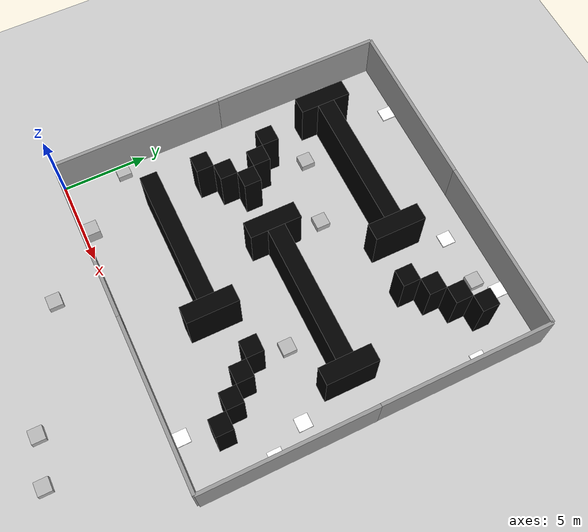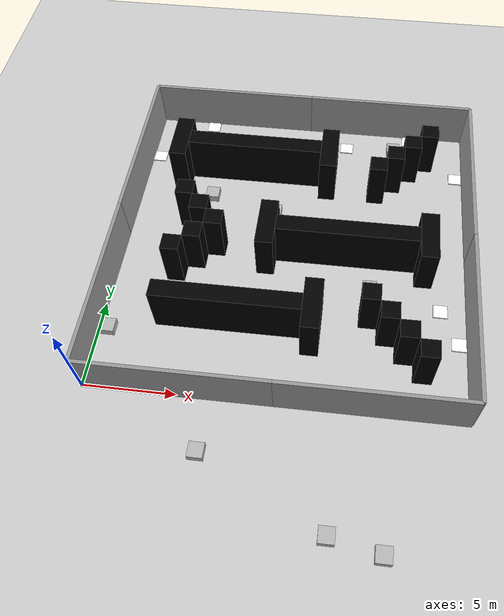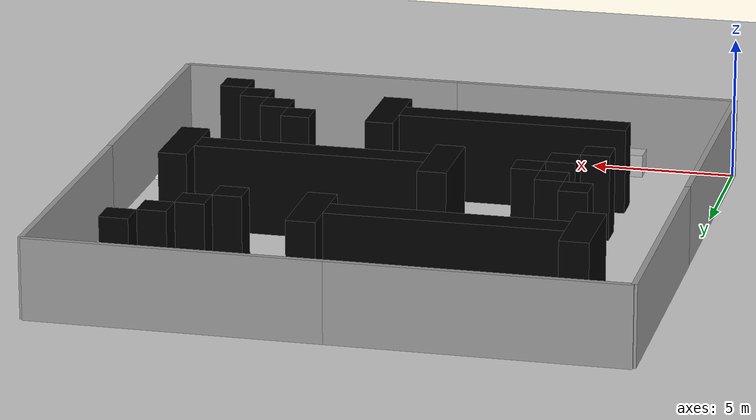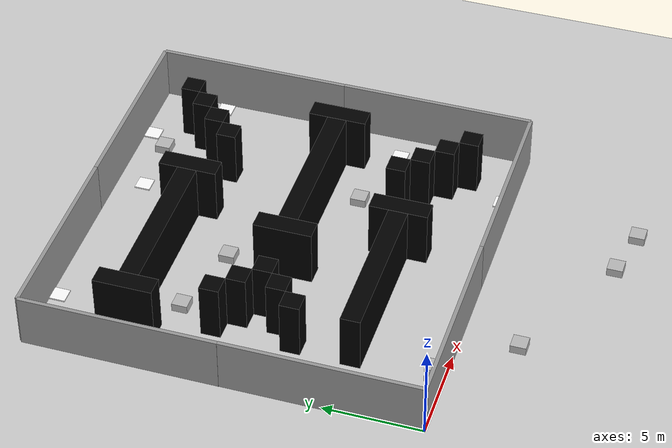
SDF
<sdf version="1.7">
 <world name="default">
  <plugin name="ros_interface_plugin" filename="librotors_gazebo_ros_interface_plugin.so"/>
  <light name="sun" type="directional">
   <pose>0 0 10 0 -0 0</pose>
   <diffuse>0.8 0.8 0.8 1</diffuse>
   <specular>0.2 0.2 0.2 1</specular>
   <attenuation>
    <range>1000</range>
    <constant>0.9</constant>
    <linear>0.01</linear>
    <quadratic>0.001</quadratic>
   </attenuation>
   <direction>-0.5 0.1 -0.9</direction>
   <spot><inner_angle>0</inner_angle><outer_angle>0</outer_angle><falloff>0</falloff></spot>
  </light>
  <model name="ground_plane">
   <static>1</static>
   <link name="link">
    <collision name="collision">
     <geometry><plane><normal>0 0 1</normal><size>100 100</size></plane></geometry>
     <surface><friction><ode><mu>100</mu><mu2>50</mu2></ode></friction></surface>
    </collision>
    <visual name="visual">
     <cast_shadows>0</cast_shadows>
     <geometry><plane><normal>0 0 1</normal><size>100 100</size></plane></geometry>
     <material>
      <script><uri>file://media/materials/scripts/gazebo.material</uri><name>Gazebo/Grey</name></script>
     </material>
    </visual>
   </link>
  </model>
  <gravity>0 0 -9.8</gravity>
  <magnetic_field>6e-06 2.3e-05 -4.2e-05</magnetic_field>
  <atmosphere type="adiabatic"/>
  <physics name="default_physics" default="0" type="ode">
   <max_step_size>0.01</max_step_size>
   <real_time_factor>1</real_time_factor>
   <real_time_update_rate>100</real_time_update_rate>
  </physics>
  <scene><ambient>0.4 0.4 0.4 1</ambient><background>0.7 0.7 0.7 1</background><shadows>1</shadows></scene>
  <audio><device>default</device></audio>
  <spherical_coordinates>
   <surface_model>EARTH_WGS84</surface_model>
   <latitude_deg>0</latitude_deg>
   <longitude_deg>0</longitude_deg>
   <elevation>0</elevation>
   <heading_deg>0</heading_deg>
  </spherical_coordinates>
  <model name="grey_wall_10">
   <link name="link">
    <pose>0 0 1.4 0 -0 0</pose>
    <inertial>
     <mass>1</mass>
     <inertia><ixx>1</ixx><ixy>0</ixy><ixz>0</ixz><iyy>1</iyy><iyz>0</iyz><izz>1</izz></inertia>
    </inertial>
    <visual name="visual">
     <cast_shadows>0</cast_shadows>
     <geometry><box><size>10 0.2 2.8</size></box></geometry>
     <material>
      <script>
       <uri>model://grey_wall/materials/scripts</uri>
       <uri>model://grey_wall/materials/textures</uri>
       <name>vrc/grey_wall</name>
      </script>
      <shader type="vertex"><normal_map>__default__</normal_map></shader>
      <ambient>1 1 1 1</ambient>
      <diffuse>1 1 1 1</diffuse>
      <specular>0 0 0 1</specular>
      <emissive>0 0 0 1</emissive>
     </material>
    </visual>
    <collision name="collision">
     <geometry><box><size>10 0.2 2.8</size></box></geometry>
     <surface>
      <friction>
       <ode><mu>1</mu><mu2>1</mu2><fdir1>0 0 0</fdir1><slip1>0</slip1><slip2>0</slip2></ode>
       <torsional>
        <coefficient>1</coefficient>
        <patch_radius>0</patch_radius>
        <surface_radius>0</surface_radius>
        <use_patch_radius>1</use_patch_radius>
        <ode><slip>0</slip></ode>
       </torsional>
      </friction>
      <bounce><restitution_coefficient>0</restitution_coefficient><threshold>1e+06</threshold></bounce>
      <contact>
       <collide_without_contact>0</collide_without_contact>
       <collide_without_contact_bitmask>1</collide_without_contact_bitmask>
       <collide_bitmask>1</collide_bitmask>
       <ode>
        <soft_cfm>0</soft_cfm>
        <soft_erp>0.2</soft_erp>
        <kp>1e+13</kp>
        <kd>1</kd>
        <max_vel>0.01</max_vel>
        <min_depth>0</min_depth>
       </ode>
       <bullet>
        <split_impulse>1</split_impulse>
        <split_impulse_penetration_threshold>-0.01</split_impulse_penetration_threshold>
        <soft_cfm>0</soft_cfm>
        <soft_erp>0.2</soft_erp>
        <kp>1e+13</kp>
        <kd>1</kd>
       </bullet>
      </contact>
     </surface>
    </collision>
   </link>
   <static>1</static>
   <pose>5 0 0 0 -0 0</pose>
  </model>
  <model name="grey_wall_10_0">
   <link name="link">
    <pose>0 0 1.4 0 -0 0</pose>
    <inertial>
     <mass>1</mass>
     <inertia><ixx>1</ixx><ixy>0</ixy><ixz>0</ixz><iyy>1</iyy><iyz>0</iyz><izz>1</izz></inertia>
    </inertial>
    <visual name="visual">
     <cast_shadows>0</cast_shadows>
     <geometry><box><size>10 0.2 2.8</size></box></geometry>
     <material>
      <script>
       <uri>model://grey_wall/materials/scripts</uri>
       <uri>model://grey_wall/materials/textures</uri>
       <name>vrc/grey_wall</name>
      </script>
      <shader type="vertex"><normal_map>__default__</normal_map></shader>
      <ambient>1 1 1 1</ambient>
      <diffuse>1 1 1 1</diffuse>
      <specular>0 0 0 1</specular>
      <emissive>0 0 0 1</emissive>
     </material>
    </visual>
    <collision name="collision">
     <geometry><box><size>10 0.2 2.8</size></box></geometry>
     <surface>
      <friction>
       <ode><mu>1</mu><mu2>1</mu2><fdir1>0 0 0</fdir1><slip1>0</slip1><slip2>0</slip2></ode>
       <torsional>
        <coefficient>1</coefficient>
        <patch_radius>0</patch_radius>
        <surface_radius>0</surface_radius>
        <use_patch_radius>1</use_patch_radius>
        <ode><slip>0</slip></ode>
       </torsional>
      </friction>
      <bounce><restitution_coefficient>0</restitution_coefficient><threshold>1e+06</threshold></bounce>
      <contact>
       <collide_without_contact>0</collide_without_contact>
       <collide_without_contact_bitmask>1</collide_without_contact_bitmask>
       <collide_bitmask>1</collide_bitmask>
       <ode>
        <soft_cfm>0</soft_cfm>
        <soft_erp>0.2</soft_erp>
        <kp>1e+13</kp>
        <kd>1</kd>
        <max_vel>0.01</max_vel>
        <min_depth>0</min_depth>
       </ode>
       <bullet>
        <split_impulse>1</split_impulse>
        <split_impulse_penetration_threshold>-0.01</split_impulse_penetration_threshold>
        <soft_cfm>0</soft_cfm>
        <soft_erp>0.2</soft_erp>
        <kp>1e+13</kp>
        <kd>1</kd>
       </bullet>
      </contact>
     </surface>
    </collision>
   </link>
   <static>1</static>
   <pose>15 20 0 0 -0 0</pose>
  </model>
  <model name="grey_wall_10_1">
   <link name="link">
    <pose>0 0 1.4 0 -0 0</pose>
    <inertial>
     <mass>1</mass>
     <inertia><ixx>1</ixx><ixy>0</ixy><ixz>0</ixz><iyy>1</iyy><iyz>0</iyz><izz>1</izz></inertia>
    </inertial>
    <visual name="visual">
     <cast_shadows>0</cast_shadows>
     <geometry><box><size>10 0.2 2.8</size></box></geometry>
     <material>
      <script>
       <uri>model://grey_wall/materials/scripts</uri>
       <uri>model://grey_wall/materials/textures</uri>
       <name>vrc/grey_wall</name>
      </script>
      <shader type="vertex"><normal_map>__default__</normal_map></shader>
      <ambient>1 1 1 1</ambient>
      <diffuse>1 1 1 1</diffuse>
      <specular>0 0 0 1</specular>
      <emissive>0 0 0 1</emissive>
     </material>
    </visual>
    <collision name="collision">
     <geometry><box><size>10 0.2 2.8</size></box></geometry>
     <surface>
      <friction>
       <ode><mu>1</mu><mu2>1</mu2><fdir1>0 0 0</fdir1><slip1>0</slip1><slip2>0</slip2></ode>
       <torsional>
        <coefficient>1</coefficient>
        <patch_radius>0</patch_radius>
        <surface_radius>0</surface_radius>
        <use_patch_radius>1</use_patch_radius>
        <ode><slip>0</slip></ode>
       </torsional>
      </friction>
      <bounce><restitution_coefficient>0</restitution_coefficient><threshold>1e+06</threshold></bounce>
      <contact>
       <collide_without_contact>0</collide_without_contact>
       <collide_without_contact_bitmask>1</collide_without_contact_bitmask>
       <collide_bitmask>1</collide_bitmask>
       <ode>
        <soft_cfm>0</soft_cfm>
        <soft_erp>0.2</soft_erp>
        <kp>1e+13</kp>
        <kd>1</kd>
        <max_vel>0.01</max_vel>
        <min_depth>0</min_depth>
       </ode>
       <bullet>
        <split_impulse>1</split_impulse>
        <split_impulse_penetration_threshold>-0.01</split_impulse_penetration_threshold>
        <soft_cfm>0</soft_cfm>
        <soft_erp>0.2</soft_erp>
        <kp>1e+13</kp>
        <kd>1</kd>
       </bullet>
      </contact>
     </surface>
    </collision>
   </link>
   <static>1</static>
   <pose>15 0 0 0 -0 0</pose>
  </model>
  <model name="grey_wall_10_2">
   <link name="link">
    <pose>0 0 1.4 0 -0 0</pose>
    <inertial>
     <mass>1</mass>
     <inertia><ixx>1</ixx><ixy>0</ixy><ixz>0</ixz><iyy>1</iyy><iyz>0</iyz><izz>1</izz></inertia>
    </inertial>
    <visual name="visual">
     <cast_shadows>0</cast_shadows>
     <geometry><box><size>10 0.2 2.8</size></box></geometry>
     <material>
      <script>
       <uri>model://grey_wall/materials/scripts</uri>
       <uri>model://grey_wall/materials/textures</uri>
       <name>vrc/grey_wall</name>
      </script>
      <shader type="vertex"><normal_map>__default__</normal_map></shader>
      <ambient>1 1 1 1</ambient>
      <diffuse>1 1 1 1</diffuse>
      <specular>0 0 0 1</specular>
      <emissive>0 0 0 1</emissive>
     </material>
    </visual>
    <collision name="collision">
     <geometry><box><size>10 0.2 2.8</size></box></geometry>
     <surface>
      <friction>
       <ode><mu>1</mu><mu2>1</mu2><fdir1>0 0 0</fdir1><slip1>0</slip1><slip2>0</slip2></ode>
       <torsional>
        <coefficient>1</coefficient>
        <patch_radius>0</patch_radius>
        <surface_radius>0</surface_radius>
        <use_patch_radius>1</use_patch_radius>
        <ode><slip>0</slip></ode>
       </torsional>
      </friction>
      <bounce><restitution_coefficient>0</restitution_coefficient><threshold>1e+06</threshold></bounce>
      <contact>
       <collide_without_contact>0</collide_without_contact>
       <collide_without_contact_bitmask>1</collide_without_contact_bitmask>
       <collide_bitmask>1</collide_bitmask>
       <ode>
        <soft_cfm>0</soft_cfm>
        <soft_erp>0.2</soft_erp>
        <kp>1e+13</kp>
        <kd>1</kd>
        <max_vel>0.01</max_vel>
        <min_depth>0</min_depth>
       </ode>
       <bullet>
        <split_impulse>1</split_impulse>
        <split_impulse_penetration_threshold>-0.01</split_impulse_penetration_threshold>
        <soft_cfm>0</soft_cfm>
        <soft_erp>0.2</soft_erp>
        <kp>1e+13</kp>
        <kd>1</kd>
       </bullet>
      </contact>
     </surface>
    </collision>
   </link>
   <static>1</static>
   <pose>0 5 0 0 -0 1.57</pose>
  </model>
  <model name="grey_wall_10_3">
   <link name="link">
    <pose>0 0 1.4 0 -0 0</pose>
    <inertial>
     <mass>1</mass>
     <inertia><ixx>1</ixx><ixy>0</ixy><ixz>0</ixz><iyy>1</iyy><iyz>0</iyz><izz>1</izz></inertia>
    </inertial>
    <visual name="visual">
     <cast_shadows>0</cast_shadows>
     <geometry><box><size>10 0.2 2.8</size></box></geometry>
     <material>
      <script>
       <uri>model://grey_wall/materials/scripts</uri>
       <uri>model://grey_wall/materials/textures</uri>
       <name>vrc/grey_wall</name>
      </script>
      <shader type="vertex"><normal_map>__default__</normal_map></shader>
      <ambient>1 1 1 1</ambient>
      <diffuse>1 1 1 1</diffuse>
      <specular>0 0 0 1</specular>
      <emissive>0 0 0 1</emissive>
     </material>
    </visual>
    <collision name="collision">
     <geometry><box><size>10 0.2 2.8</size></box></geometry>
     <surface>
      <friction>
       <ode><mu>1</mu><mu2>1</mu2><fdir1>0 0 0</fdir1><slip1>0</slip1><slip2>0</slip2></ode>
       <torsional>
        <coefficient>1</coefficient>
        <patch_radius>0</patch_radius>
        <surface_radius>0</surface_radius>
        <use_patch_radius>1</use_patch_radius>
        <ode><slip>0</slip></ode>
       </torsional>
      </friction>
      <bounce><restitution_coefficient>0</restitution_coefficient><threshold>1e+06</threshold></bounce>
      <contact>
       <collide_without_contact>0</collide_without_contact>
       <collide_without_contact_bitmask>1</collide_without_contact_bitmask>
       <collide_bitmask>1</collide_bitmask>
       <ode>
        <soft_cfm>0</soft_cfm>
        <soft_erp>0.2</soft_erp>
        <kp>1e+13</kp>
        <kd>1</kd>
        <max_vel>0.01</max_vel>
        <min_depth>0</min_depth>
       </ode>
       <bullet>
        <split_impulse>1</split_impulse>
        <split_impulse_penetration_threshold>-0.01</split_impulse_penetration_threshold>
        <soft_cfm>0</soft_cfm>
        <soft_erp>0.2</soft_erp>
        <kp>1e+13</kp>
        <kd>1</kd>
       </bullet>
      </contact>
     </surface>
    </collision>
   </link>
   <static>1</static>
   <pose>20 5 0 0 -0 1.57</pose>
  </model>
  <model name="grey_wall_10_4">
   <link name="link">
    <pose>0 0 1.4 0 -0 0</pose>
    <inertial>
     <mass>1</mass>
     <inertia><ixx>1</ixx><ixy>0</ixy><ixz>0</ixz><iyy>1</iyy><iyz>0</iyz><izz>1</izz></inertia>
    </inertial>
    <visual name="visual">
     <cast_shadows>0</cast_shadows>
     <geometry><box><size>10 0.2 2.8</size></box></geometry>
     <material>
      <script>
       <uri>model://grey_wall/materials/scripts</uri>
       <uri>model://grey_wall/materials/textures</uri>
       <name>vrc/grey_wall</name>
      </script>
      <shader type="vertex"><normal_map>__default__</normal_map></shader>
      <ambient>1 1 1 1</ambient>
      <diffuse>1 1 1 1</diffuse>
      <specular>0 0 0 1</specular>
      <emissive>0 0 0 1</emissive>
     </material>
    </visual>
    <collision name="collision">
     <geometry><box><size>10 0.2 2.8</size></box></geometry>
     <surface>
      <friction>
       <ode><mu>1</mu><mu2>1</mu2><fdir1>0 0 0</fdir1><slip1>0</slip1><slip2>0</slip2></ode>
       <torsional>
        <coefficient>1</coefficient>
        <patch_radius>0</patch_radius>
        <surface_radius>0</surface_radius>
        <use_patch_radius>1</use_patch_radius>
        <ode><slip>0</slip></ode>
       </torsional>
      </friction>
      <bounce><restitution_coefficient>0</restitution_coefficient><threshold>1e+06</threshold></bounce>
      <contact>
       <collide_without_contact>0</collide_without_contact>
       <collide_without_contact_bitmask>1</collide_without_contact_bitmask>
       <collide_bitmask>1</collide_bitmask>
       <ode>
        <soft_cfm>0</soft_cfm>
        <soft_erp>0.2</soft_erp>
        <kp>1e+13</kp>
        <kd>1</kd>
        <max_vel>0.01</max_vel>
        <min_depth>0</min_depth>
       </ode>
       <bullet>
        <split_impulse>1</split_impulse>
        <split_impulse_penetration_threshold>-0.01</split_impulse_penetration_threshold>
        <soft_cfm>0</soft_cfm>
        <soft_erp>0.2</soft_erp>
        <kp>1e+13</kp>
        <kd>1</kd>
       </bullet>
      </contact>
     </surface>
    </collision>
   </link>
   <static>1</static>
   <pose>0 15 0 0 -0 1.57</pose>
  </model>
  <model name="grey_wall_10_5">
   <link name="link">
    <pose>0 0 1.4 0 -0 0</pose>
    <inertial>
     <mass>1</mass>
     <inertia><ixx>1</ixx><ixy>0</ixy><ixz>0</ixz><iyy>1</iyy><iyz>0</iyz><izz>1</izz></inertia>
    </inertial>
    <visual name="visual">
     <cast_shadows>0</cast_shadows>
     <geometry><box><size>10 0.2 2.8</size></box></geometry>
     <material>
      <script>
       <uri>model://grey_wall/materials/scripts</uri>
       <uri>model://grey_wall/materials/textures</uri>
       <name>vrc/grey_wall</name>
      </script>
      <shader type="vertex"><normal_map>__default__</normal_map></shader>
      <ambient>1 1 1 1</ambient>
      <diffuse>1 1 1 1</diffuse>
      <specular>0 0 0 1</specular>
      <emissive>0 0 0 1</emissive>
     </material>
    </visual>
    <collision name="collision">
     <geometry><box><size>10 0.2 2.8</size></box></geometry>
     <surface>
      <friction>
       <ode><mu>1</mu><mu2>1</mu2><fdir1>0 0 0</fdir1><slip1>0</slip1><slip2>0</slip2></ode>
       <torsional>
        <coefficient>1</coefficient>
        <patch_radius>0</patch_radius>
        <surface_radius>0</surface_radius>
        <use_patch_radius>1</use_patch_radius>
        <ode><slip>0</slip></ode>
       </torsional>
      </friction>
      <bounce><restitution_coefficient>0</restitution_coefficient><threshold>1e+06</threshold></bounce>
      <contact>
       <collide_without_contact>0</collide_without_contact>
       <collide_without_contact_bitmask>1</collide_without_contact_bitmask>
       <collide_bitmask>1</collide_bitmask>
       <ode>
        <soft_cfm>0</soft_cfm>
        <soft_erp>0.2</soft_erp>
        <kp>1e+13</kp>
        <kd>1</kd>
        <max_vel>0.01</max_vel>
        <min_depth>0</min_depth>
       </ode>
       <bullet>
        <split_impulse>1</split_impulse>
        <split_impulse_penetration_threshold>-0.01</split_impulse_penetration_threshold>
        <soft_cfm>0</soft_cfm>
        <soft_erp>0.2</soft_erp>
        <kp>1e+13</kp>
        <kd>1</kd>
       </bullet>
      </contact>
     </surface>
    </collision>
   </link>
   <static>1</static>
   <pose>20 15 0 0 -0 1.57</pose>
  </model>
  <model name="grey_wall_10_6">
   <link name="link">
    <pose>0 0 1.4 0 -0 0</pose>
    <inertial>
     <mass>1</mass>
     <inertia><ixx>1</ixx><ixy>0</ixy><ixz>0</ixz><iyy>1</iyy><iyz>0</iyz><izz>1</izz></inertia>
    </inertial>
    <visual name="visual">
     <cast_shadows>0</cast_shadows>
     <geometry><box><size>10 0.2 2.8</size></box></geometry>
     <material>
      <script>
       <uri>model://grey_wall/materials/scripts</uri>
       <uri>model://grey_wall/materials/textures</uri>
       <name>vrc/grey_wall</name>
      </script>
      <shader type="vertex"><normal_map>__default__</normal_map></shader>
      <ambient>1 1 1 1</ambient>
      <diffuse>1 1 1 1</diffuse>
      <specular>0 0 0 1</specular>
      <emissive>0 0 0 1</emissive>
     </material>
    </visual>
    <collision name="collision">
     <geometry><box><size>10 0.2 2.8</size></box></geometry>
     <surface>
      <friction>
       <ode><mu>1</mu><mu2>1</mu2><fdir1>0 0 0</fdir1><slip1>0</slip1><slip2>0</slip2></ode>
       <torsional>
        <coefficient>1</coefficient>
        <patch_radius>0</patch_radius>
        <surface_radius>0</surface_radius>
        <use_patch_radius>1</use_patch_radius>
        <ode><slip>0</slip></ode>
       </torsional>
      </friction>
      <bounce><restitution_coefficient>0</restitution_coefficient><threshold>1e+06</threshold></bounce>
      <contact>
       <collide_without_contact>0</collide_without_contact>
       <collide_without_contact_bitmask>1</collide_without_contact_bitmask>
       <collide_bitmask>1</collide_bitmask>
       <ode>
        <soft_cfm>0</soft_cfm>
        <soft_erp>0.2</soft_erp>
        <kp>1e+13</kp>
        <kd>1</kd>
        <max_vel>0.01</max_vel>
        <min_depth>0</min_depth>
       </ode>
       <bullet>
        <split_impulse>1</split_impulse>
        <split_impulse_penetration_threshold>-0.01</split_impulse_penetration_threshold>
        <soft_cfm>0</soft_cfm>
        <soft_erp>0.2</soft_erp>
        <kp>1e+13</kp>
        <kd>1</kd>
       </bullet>
      </contact>
     </surface>
    </collision>
   </link>
   <static>1</static>
   <pose>5 20 0 0 -0 0</pose>
  </model>
  <model name="brick_box_8x1_b">
   <link name="chassis">
    <pose>0 0 1.5 0 -0 0</pose>
    <inertial>
     <mass>1</mass>
     <inertia><ixx>1</ixx><ixy>0</ixy><ixz>0</ixz><iyy>1</iyy><iyz>0</iyz><izz>1</izz></inertia>
    </inertial>
    <visual name="visual">
     <geometry><mesh><uri>model://brick_box_3x1x3/meshes/simple_box.dae</uri><scale>8 1 3</scale></mesh></geometry>
     <material>
      <script>
       <uri>model://brick_box_3x1x3/materials/scripts</uri>
       <uri>model://brick_box_3x1x3/materials/textures</uri>
       <name>BrickBox/Diffuse</name>
      </script>
      <shader type="vertex"><normal_map>__default__</normal_map></shader>
      <ambient>0 0 0 1</ambient>
      <diffuse>0 0 0 1</diffuse>
      <specular>0 0 0 1</specular>
      <emissive>0 0 0 1</emissive>
      <lighting>1</lighting>
     </material>
    </visual>
    <collision name="collision">
     <geometry><box><size>8 1 3</size></box></geometry>
     <surface>
      <friction>
       <ode><mu>1</mu><mu2>1</mu2><fdir1>0 0 0</fdir1><slip1>0</slip1><slip2>0</slip2></ode>
       <torsional>
        <coefficient>1</coefficient>
        <patch_radius>0</patch_radius>
        <surface_radius>0</surface_radius>
        <use_patch_radius>1</use_patch_radius>
        <ode><slip>0</slip></ode>
       </torsional>
      </friction>
      <bounce><restitution_coefficient>0</restitution_coefficient><threshold>1e+06</threshold></bounce>
      <contact>
       <collide_without_contact>0</collide_without_contact>
       <collide_without_contact_bitmask>1</collide_without_contact_bitmask>
       <collide_bitmask>1</collide_bitmask>
       <ode>
        <soft_cfm>0</soft_cfm>
        <soft_erp>0.2</soft_erp>
        <kp>1e+13</kp>
        <kd>1</kd>
        <max_vel>0.01</max_vel>
        <min_depth>0</min_depth>
       </ode>
       <bullet>
        <split_impulse>1</split_impulse>
        <split_impulse_penetration_threshold>-0.01</split_impulse_penetration_threshold>
        <soft_cfm>0</soft_cfm>
        <soft_erp>0.2</soft_erp>
        <kp>1e+13</kp>
        <kd>1</kd>
       </bullet>
      </contact>
     </surface>
    </collision>
   </link>
   <static>1</static>
   <pose>7 4.5 0 0 -0 0</pose>
  </model>
  <model name="brick_box_8x1_b_0">
   <link name="chassis">
    <pose>0 0 1.5 0 -0 0</pose>
    <inertial>
     <mass>1</mass>
     <inertia><ixx>1</ixx><ixy>0</ixy><ixz>0</ixz><iyy>1</iyy><iyz>0</iyz><izz>1</izz></inertia>
    </inertial>
    <visual name="visual">
     <geometry><mesh><uri>model://brick_box_3x1x3/meshes/simple_box.dae</uri><scale>8 1 3</scale></mesh></geometry>
     <material>
      <script>
       <uri>model://brick_box_3x1x3/materials/scripts</uri>
       <uri>model://brick_box_3x1x3/materials/textures</uri>
       <name>BrickBox/Diffuse</name>
      </script>
      <shader type="vertex"><normal_map>__default__</normal_map></shader>
      <ambient>0 0 0 1</ambient>
      <diffuse>0 0 0 1</diffuse>
      <specular>0 0 0 1</specular>
      <emissive>0 0 0 1</emissive>
      <lighting>1</lighting>
     </material>
    </visual>
    <collision name="collision">
     <geometry><box><size>8 1 3</size></box></geometry>
     <surface>
      <friction>
       <ode><mu>1</mu><mu2>1</mu2><fdir1>0 0 0</fdir1><slip1>0</slip1><slip2>0</slip2></ode>
       <torsional>
        <coefficient>1</coefficient>
        <patch_radius>0</patch_radius>
        <surface_radius>0</surface_radius>
        <use_patch_radius>1</use_patch_radius>
        <ode><slip>0</slip></ode>
       </torsional>
      </friction>
      <bounce><restitution_coefficient>0</restitution_coefficient><threshold>1e+06</threshold></bounce>
      <contact>
       <collide_without_contact>0</collide_without_contact>
       <collide_without_contact_bitmask>1</collide_without_contact_bitmask>
       <collide_bitmask>1</collide_bitmask>
       <ode>
        <soft_cfm>0</soft_cfm>
        <soft_erp>0.2</soft_erp>
        <kp>1e+13</kp>
        <kd>1</kd>
        <max_vel>0.01</max_vel>
        <min_depth>0</min_depth>
       </ode>
       <bullet>
        <split_impulse>1</split_impulse>
        <split_impulse_penetration_threshold>-0.01</split_impulse_penetration_threshold>
        <soft_cfm>0</soft_cfm>
        <soft_erp>0.2</soft_erp>
        <kp>1e+13</kp>
        <kd>1</kd>
       </bullet>
      </contact>
     </surface>
    </collision>
   </link>
   <static>1</static>
   <pose>13 9.5 0 0 -0 0</pose>
  </model>
  <model name="brick_box_8x1_b_1">
   <link name="chassis">
    <pose>0 0 1.5 0 -0 0</pose>
    <inertial>
     <mass>1</mass>
     <inertia><ixx>1</ixx><ixy>0</ixy><ixz>0</ixz><iyy>1</iyy><iyz>0</iyz><izz>1</izz></inertia>
    </inertial>
    <visual name="visual">
     <geometry><mesh><uri>model://brick_box_3x1x3/meshes/simple_box.dae</uri><scale>8 1 3</scale></mesh></geometry>
     <material>
      <script>
       <uri>model://brick_box_3x1x3/materials/scripts</uri>
       <uri>model://brick_box_3x1x3/materials/textures</uri>
       <name>BrickBox/Diffuse</name>
      </script>
      <shader type="vertex"><normal_map>__default__</normal_map></shader>
      <ambient>0 0 0 1</ambient>
      <diffuse>0 0 0 1</diffuse>
      <specular>0 0 0 1</specular>
      <emissive>0 0 0 1</emissive>
      <lighting>1</lighting>
     </material>
    </visual>
    <collision name="collision">
     <geometry><box><size>8 1 3</size></box></geometry>
     <surface>
      <friction>
       <ode><mu>1</mu><mu2>1</mu2><fdir1>0 0 0</fdir1><slip1>0</slip1><slip2>0</slip2></ode>
       <torsional>
        <coefficient>1</coefficient>
        <patch_radius>0</patch_radius>
        <surface_radius>0</surface_radius>
        <use_patch_radius>1</use_patch_radius>
        <ode><slip>0</slip></ode>
       </torsional>
      </friction>
      <bounce><restitution_coefficient>0</restitution_coefficient><threshold>1e+06</threshold></bounce>
      <contact>
       <collide_without_contact>0</collide_without_contact>
       <collide_without_contact_bitmask>1</collide_without_contact_bitmask>
       <collide_bitmask>1</collide_bitmask>
       <ode>
        <soft_cfm>0</soft_cfm>
        <soft_erp>0.2</soft_erp>
        <kp>1e+13</kp>
        <kd>1</kd>
        <max_vel>0.01</max_vel>
        <min_depth>0</min_depth>
       </ode>
       <bullet>
        <split_impulse>1</split_impulse>
        <split_impulse_penetration_threshold>-0.01</split_impulse_penetration_threshold>
        <soft_cfm>0</soft_cfm>
        <soft_erp>0.2</soft_erp>
        <kp>1e+13</kp>
        <kd>1</kd>
       </bullet>
      </contact>
     </surface>
    </collision>
   </link>
   <static>1</static>
   <pose>7 15.5 0 0 -0 0</pose>
  </model>
  <model name="brick_box_3x1x3_black">
   <link name="chassis">
    <pose>0 0 1.5 0 -0 0</pose>
    <inertial>
     <mass>1</mass>
     <inertia><ixx>1</ixx><ixy>0</ixy><ixz>0</ixz><iyy>1</iyy><iyz>0</iyz><izz>1</izz></inertia>
    </inertial>
    <visual name="visual">
     <geometry><mesh><uri>model://brick_box_3x1x3/meshes/simple_box.dae</uri><scale>3 1 3</scale></mesh></geometry>
     <material>
      <script>
       <uri>model://brick_box_3x1x3/materials/scripts</uri>
       <uri>model://brick_box_3x1x3/materials/textures</uri>
       <name>BrickBox/Diffuse</name>
      </script>
      <shader type="vertex"><normal_map>__default__</normal_map></shader>
      <ambient>0 0 0 1</ambient>
      <diffuse>0 0 0 1</diffuse>
      <specular>0 0 0 1</specular>
      <emissive>0 0 0 1</emissive>
      <lighting>1</lighting>
     </material>
    </visual>
    <collision name="collision">
     <geometry><box><size>3 1 3</size></box></geometry>
     <surface>
      <friction>
       <ode><mu>1</mu><mu2>1</mu2><fdir1>0 0 0</fdir1><slip1>0</slip1><slip2>0</slip2></ode>
       <torsional>
        <coefficient>1</coefficient>
        <patch_radius>0</patch_radius>
        <surface_radius>0</surface_radius>
        <use_patch_radius>1</use_patch_radius>
        <ode><slip>0</slip></ode>
       </torsional>
      </friction>
      <bounce><restitution_coefficient>0</restitution_coefficient><threshold>1e+06</threshold></bounce>
      <contact>
       <collide_without_contact>0</collide_without_contact>
       <collide_without_contact_bitmask>1</collide_without_contact_bitmask>
       <collide_bitmask>1</collide_bitmask>
       <ode>
        <soft_cfm>0</soft_cfm>
        <soft_erp>0.2</soft_erp>
        <kp>1e+13</kp>
        <kd>1</kd>
        <max_vel>0.01</max_vel>
        <min_depth>0</min_depth>
       </ode>
       <bullet>
        <split_impulse>1</split_impulse>
        <split_impulse_penetration_threshold>-0.01</split_impulse_penetration_threshold>
        <soft_cfm>0</soft_cfm>
        <soft_erp>0.2</soft_erp>
        <kp>1e+13</kp>
        <kd>1</kd>
       </bullet>
      </contact>
     </surface>
    </collision>
   </link>
   <static>1</static>
   <pose>2.5 15.5 0 0 -0 1.57</pose>
  </model>
  <model name="brick_box_3x1x3_black_0">
   <link name="chassis">
    <pose>0 0 1.5 0 -0 0</pose>
    <inertial>
     <mass>1</mass>
     <inertia><ixx>1</ixx><ixy>0</ixy><ixz>0</ixz><iyy>1</iyy><iyz>0</iyz><izz>1</izz></inertia>
    </inertial>
    <visual name="visual">
     <geometry><mesh><uri>model://brick_box_3x1x3/meshes/simple_box.dae</uri><scale>3 1 3</scale></mesh></geometry>
     <material>
      <script>
       <uri>model://brick_box_3x1x3/materials/scripts</uri>
       <uri>model://brick_box_3x1x3/materials/textures</uri>
       <name>BrickBox/Diffuse</name>
      </script>
      <shader type="vertex"><normal_map>__default__</normal_map></shader>
      <ambient>0 0 0 1</ambient>
      <diffuse>0 0 0 1</diffuse>
      <specular>0 0 0 1</specular>
      <emissive>0 0 0 1</emissive>
      <lighting>1</lighting>
     </material>
    </visual>
    <collision name="collision">
     <geometry><box><size>3 1 3</size></box></geometry>
     <surface>
      <friction>
       <ode><mu>1</mu><mu2>1</mu2><fdir1>0 0 0</fdir1><slip1>0</slip1><slip2>0</slip2></ode>
       <torsional>
        <coefficient>1</coefficient>
        <patch_radius>0</patch_radius>
        <surface_radius>0</surface_radius>
        <use_patch_radius>1</use_patch_radius>
        <ode><slip>0</slip></ode>
       </torsional>
      </friction>
      <bounce><restitution_coefficient>0</restitution_coefficient><threshold>1e+06</threshold></bounce>
      <contact>
       <collide_without_contact>0</collide_without_contact>
       <collide_without_contact_bitmask>1</collide_without_contact_bitmask>
       <collide_bitmask>1</collide_bitmask>
       <ode>
        <soft_cfm>0</soft_cfm>
        <soft_erp>0.2</soft_erp>
        <kp>1e+13</kp>
        <kd>1</kd>
        <max_vel>0.01</max_vel>
        <min_depth>0</min_depth>
       </ode>
       <bullet>
        <split_impulse>1</split_impulse>
        <split_impulse_penetration_threshold>-0.01</split_impulse_penetration_threshold>
        <soft_cfm>0</soft_cfm>
        <soft_erp>0.2</soft_erp>
        <kp>1e+13</kp>
        <kd>1</kd>
       </bullet>
      </contact>
     </surface>
    </collision>
   </link>
   <static>1</static>
   <pose>11.5 15.5 0 0 -0 1.57</pose>
  </model>
  <model name="brick_box_3x1x3_black_1">
   <link name="chassis">
    <pose>0 0 1.5 0 -0 0</pose>
    <inertial>
     <mass>1</mass>
     <inertia><ixx>1</ixx><ixy>0</ixy><ixz>0</ixz><iyy>1</iyy><iyz>0</iyz><izz>1</izz></inertia>
    </inertial>
    <visual name="visual">
     <geometry><mesh><uri>model://brick_box_3x1x3/meshes/simple_box.dae</uri><scale>3 1 3</scale></mesh></geometry>
     <material>
      <script>
       <uri>model://brick_box_3x1x3/materials/scripts</uri>
       <uri>model://brick_box_3x1x3/materials/textures</uri>
       <name>BrickBox/Diffuse</name>
      </script>
      <shader type="vertex"><normal_map>__default__</normal_map></shader>
      <ambient>0 0 0 1</ambient>
      <diffuse>0 0 0 1</diffuse>
      <specular>0 0 0 1</specular>
      <emissive>0 0 0 1</emissive>
      <lighting>1</lighting>
     </material>
    </visual>
    <collision name="collision">
     <geometry><box><size>3 1 3</size></box></geometry>
     <surface>
      <friction>
       <ode><mu>1</mu><mu2>1</mu2><fdir1>0 0 0</fdir1><slip1>0</slip1><slip2>0</slip2></ode>
       <torsional>
        <coefficient>1</coefficient>
        <patch_radius>0</patch_radius>
        <surface_radius>0</surface_radius>
        <use_patch_radius>1</use_patch_radius>
        <ode><slip>0</slip></ode>
       </torsional>
      </friction>
      <bounce><restitution_coefficient>0</restitution_coefficient><threshold>1e+06</threshold></bounce>
      <contact>
       <collide_without_contact>0</collide_without_contact>
       <collide_without_contact_bitmask>1</collide_without_contact_bitmask>
       <collide_bitmask>1</collide_bitmask>
       <ode>
        <soft_cfm>0</soft_cfm>
        <soft_erp>0.2</soft_erp>
        <kp>1e+13</kp>
        <kd>1</kd>
        <max_vel>0.01</max_vel>
        <min_depth>0</min_depth>
       </ode>
       <bullet>
        <split_impulse>1</split_impulse>
        <split_impulse_penetration_threshold>-0.01</split_impulse_penetration_threshold>
        <soft_cfm>0</soft_cfm>
        <soft_erp>0.2</soft_erp>
        <kp>1e+13</kp>
        <kd>1</kd>
       </bullet>
      </contact>
     </surface>
    </collision>
   </link>
   <static>1</static>
   <pose>17.5 9.5 0 0 -0 1.57</pose>
  </model>
  <model name="brick_box_3x1x3_black_2">
   <link name="chassis">
    <pose>0 0 1.5 0 -0 0</pose>
    <inertial>
     <mass>1</mass>
     <inertia><ixx>1</ixx><ixy>0</ixy><ixz>0</ixz><iyy>1</iyy><iyz>0</iyz><izz>1</izz></inertia>
    </inertial>
    <visual name="visual">
     <geometry><mesh><uri>model://brick_box_3x1x3/meshes/simple_box.dae</uri><scale>3 1 3</scale></mesh></geometry>
     <material>
      <script>
       <uri>model://brick_box_3x1x3/materials/scripts</uri>
       <uri>model://brick_box_3x1x3/materials/textures</uri>
       <name>BrickBox/Diffuse</name>
      </script>
      <shader type="vertex"><normal_map>__default__</normal_map></shader>
      <ambient>0 0 0 1</ambient>
      <diffuse>0 0 0 1</diffuse>
      <specular>0 0 0 1</specular>
      <emissive>0 0 0 1</emissive>
      <lighting>1</lighting>
     </material>
    </visual>
    <collision name="collision">
     <geometry><box><size>3 1 3</size></box></geometry>
     <surface>
      <friction>
       <ode><mu>1</mu><mu2>1</mu2><fdir1>0 0 0</fdir1><slip1>0</slip1><slip2>0</slip2></ode>
       <torsional>
        <coefficient>1</coefficient>
        <patch_radius>0</patch_radius>
        <surface_radius>0</surface_radius>
        <use_patch_radius>1</use_patch_radius>
        <ode><slip>0</slip></ode>
       </torsional>
      </friction>
      <bounce><restitution_coefficient>0</restitution_coefficient><threshold>1e+06</threshold></bounce>
      <contact>
       <collide_without_contact>0</collide_without_contact>
       <collide_without_contact_bitmask>1</collide_without_contact_bitmask>
       <collide_bitmask>1</collide_bitmask>
       <ode>
        <soft_cfm>0</soft_cfm>
        <soft_erp>0.2</soft_erp>
        <kp>1e+13</kp>
        <kd>1</kd>
        <max_vel>0.01</max_vel>
        <min_depth>0</min_depth>
       </ode>
       <bullet>
        <split_impulse>1</split_impulse>
        <split_impulse_penetration_threshold>-0.01</split_impulse_penetration_threshold>
        <soft_cfm>0</soft_cfm>
        <soft_erp>0.2</soft_erp>
        <kp>1e+13</kp>
        <kd>1</kd>
       </bullet>
      </contact>
     </surface>
    </collision>
   </link>
   <static>1</static>
   <pose>8.5 9.5 0 0 -0 1.57</pose>
  </model>
  <model name="brick_box_3x1x3_black_3">
   <link name="chassis">
    <pose>0 0 1.5 0 -0 0</pose>
    <inertial>
     <mass>1</mass>
     <inertia><ixx>1</ixx><ixy>0</ixy><ixz>0</ixz><iyy>1</iyy><iyz>0</iyz><izz>1</izz></inertia>
    </inertial>
    <visual name="visual">
     <geometry><mesh><uri>model://brick_box_3x1x3/meshes/simple_box.dae</uri><scale>3 1 3</scale></mesh></geometry>
     <material>
      <script>
       <uri>model://brick_box_3x1x3/materials/scripts</uri>
       <uri>model://brick_box_3x1x3/materials/textures</uri>
       <name>BrickBox/Diffuse</name>
      </script>
      <shader type="vertex"><normal_map>__default__</normal_map></shader>
      <ambient>0 0 0 1</ambient>
      <diffuse>0 0 0 1</diffuse>
      <specular>0 0 0 1</specular>
      <emissive>0 0 0 1</emissive>
      <lighting>1</lighting>
     </material>
    </visual>
    <collision name="collision">
     <geometry><box><size>3 1 3</size></box></geometry>
     <surface>
      <friction>
       <ode><mu>1</mu><mu2>1</mu2><fdir1>0 0 0</fdir1><slip1>0</slip1><slip2>0</slip2></ode>
       <torsional>
        <coefficient>1</coefficient>
        <patch_radius>0</patch_radius>
        <surface_radius>0</surface_radius>
        <use_patch_radius>1</use_patch_radius>
        <ode><slip>0</slip></ode>
       </torsional>
      </friction>
      <bounce><restitution_coefficient>0</restitution_coefficient><threshold>1e+06</threshold></bounce>
      <contact>
       <collide_without_contact>0</collide_without_contact>
       <collide_without_contact_bitmask>1</collide_without_contact_bitmask>
       <collide_bitmask>1</collide_bitmask>
       <ode>
        <soft_cfm>0</soft_cfm>
        <soft_erp>0.2</soft_erp>
        <kp>1e+13</kp>
        <kd>1</kd>
        <max_vel>0.01</max_vel>
        <min_depth>0</min_depth>
       </ode>
       <bullet>
        <split_impulse>1</split_impulse>
        <split_impulse_penetration_threshold>-0.01</split_impulse_penetration_threshold>
        <soft_cfm>0</soft_cfm>
        <soft_erp>0.2</soft_erp>
        <kp>1e+13</kp>
        <kd>1</kd>
       </bullet>
      </contact>
     </surface>
    </collision>
   </link>
   <static>1</static>
   <pose>11.5 4.5 0 0 -0 1.57</pose>
  </model>
  <model name="brick_box_1_B">
   <link name="chassis">
    <pose>0 0 1.5 0 -0 0</pose>
    <inertial>
     <mass>1</mass>
     <inertia><ixx>1</ixx><ixy>0</ixy><ixz>0</ixz><iyy>1</iyy><iyz>0</iyz><izz>1</izz></inertia>
    </inertial>
    <visual name="visual">
     <geometry><mesh><uri>model://brick_box_3x1x3/meshes/simple_box.dae</uri><scale>1 1 3</scale></mesh></geometry>
     <material>
      <script>
       <uri>model://brick_box_3x1x3/materials/scripts</uri>
       <uri>model://brick_box_3x1x3/materials/textures</uri>
       <name>BrickBox/Diffuse</name>
      </script>
      <shader type="vertex"><normal_map>__default__</normal_map></shader>
      <ambient>0 0 0 1</ambient>
      <diffuse>0 0 0 1</diffuse>
      <specular>0 0 0 1</specular>
      <emissive>0 0 0 1</emissive>
      <lighting>1</lighting>
     </material>
    </visual>
    <collision name="collision">
     <geometry><box><size>1 1 3</size></box></geometry>
     <surface>
      <friction>
       <ode><mu>1</mu><mu2>1</mu2><fdir1>0 0 0</fdir1><slip1>0</slip1><slip2>0</slip2></ode>
       <torsional>
        <coefficient>1</coefficient>
        <patch_radius>0</patch_radius>
        <surface_radius>0</surface_radius>
        <use_patch_radius>1</use_patch_radius>
        <ode><slip>0</slip></ode>
       </torsional>
      </friction>
      <bounce><restitution_coefficient>0</restitution_coefficient><threshold>1e+06</threshold></bounce>
      <contact>
       <collide_without_contact>0</collide_without_contact>
       <collide_without_contact_bitmask>1</collide_without_contact_bitmask>
       <collide_bitmask>1</collide_bitmask>
       <ode>
        <soft_cfm>0</soft_cfm>
        <soft_erp>0.2</soft_erp>
        <kp>1e+13</kp>
        <kd>1</kd>
        <max_vel>0.01</max_vel>
        <min_depth>0</min_depth>
       </ode>
       <bullet>
        <split_impulse>1</split_impulse>
        <split_impulse_penetration_threshold>-0.01</split_impulse_penetration_threshold>
        <soft_cfm>0</soft_cfm>
        <soft_erp>0.2</soft_erp>
        <kp>1e+13</kp>
        <kd>1</kd>
       </bullet>
      </contact>
     </surface>
    </collision>
   </link>
   <static>1</static>
   <pose>17.5 17.5 0 0 -0 0</pose>
  </model>
  <model name="brick_box_1_B_0">
   <link name="chassis">
    <pose>0 0 1.5 0 -0 0</pose>
    <inertial>
     <mass>1</mass>
     <inertia><ixx>1</ixx><ixy>0</ixy><ixz>0</ixz><iyy>1</iyy><iyz>0</iyz><izz>1</izz></inertia>
    </inertial>
    <visual name="visual">
     <geometry><mesh><uri>model://brick_box_3x1x3/meshes/simple_box.dae</uri><scale>1 1 3</scale></mesh></geometry>
     <material>
      <script>
       <uri>model://brick_box_3x1x3/materials/scripts</uri>
       <uri>model://brick_box_3x1x3/materials/textures</uri>
       <name>BrickBox/Diffuse</name>
      </script>
      <shader type="vertex"><normal_map>__default__</normal_map></shader>
      <ambient>0 0 0 1</ambient>
      <diffuse>0 0 0 1</diffuse>
      <specular>0 0 0 1</specular>
      <emissive>0 0 0 1</emissive>
      <lighting>1</lighting>
     </material>
    </visual>
    <collision name="collision">
     <geometry><box><size>1 1 3</size></box></geometry>
     <surface>
      <friction>
       <ode><mu>1</mu><mu2>1</mu2><fdir1>0 0 0</fdir1><slip1>0</slip1><slip2>0</slip2></ode>
       <torsional>
        <coefficient>1</coefficient>
        <patch_radius>0</patch_radius>
        <surface_radius>0</surface_radius>
        <use_patch_radius>1</use_patch_radius>
        <ode><slip>0</slip></ode>
       </torsional>
      </friction>
      <bounce><restitution_coefficient>0</restitution_coefficient><threshold>1e+06</threshold></bounce>
      <contact>
       <collide_without_contact>0</collide_without_contact>
       <collide_without_contact_bitmask>1</collide_without_contact_bitmask>
       <collide_bitmask>1</collide_bitmask>
       <ode>
        <soft_cfm>0</soft_cfm>
        <soft_erp>0.2</soft_erp>
        <kp>1e+13</kp>
        <kd>1</kd>
        <max_vel>0.01</max_vel>
        <min_depth>0</min_depth>
       </ode>
       <bullet>
        <split_impulse>1</split_impulse>
        <split_impulse_penetration_threshold>-0.01</split_impulse_penetration_threshold>
        <soft_cfm>0</soft_cfm>
        <soft_erp>0.2</soft_erp>
        <kp>1e+13</kp>
        <kd>1</kd>
       </bullet>
      </contact>
     </surface>
    </collision>
   </link>
   <static>1</static>
   <pose>17.5 2.5 0 0 -0 0</pose>
  </model>
  <model name="brick_box_1_B_1">
   <link name="chassis">
    <pose>0 0 1.5 0 -0 0</pose>
    <inertial>
     <mass>1</mass>
     <inertia><ixx>1</ixx><ixy>0</ixy><ixz>0</ixz><iyy>1</iyy><iyz>0</iyz><izz>1</izz></inertia>
    </inertial>
    <visual name="visual">
     <geometry><mesh><uri>model://brick_box_3x1x3/meshes/simple_box.dae</uri><scale>1 1 3</scale></mesh></geometry>
     <material>
      <script>
       <uri>model://brick_box_3x1x3/materials/scripts</uri>
       <uri>model://brick_box_3x1x3/materials/textures</uri>
       <name>BrickBox/Diffuse</name>
      </script>
      <shader type="vertex"><normal_map>__default__</normal_map></shader>
      <ambient>0 0 0 1</ambient>
      <diffuse>0 0 0 1</diffuse>
      <specular>0 0 0 1</specular>
      <emissive>0 0 0 1</emissive>
      <lighting>1</lighting>
     </material>
    </visual>
    <collision name="collision">
     <geometry><box><size>1 1 3</size></box></geometry>
     <surface>
      <friction>
       <ode><mu>1</mu><mu2>1</mu2><fdir1>0 0 0</fdir1><slip1>0</slip1><slip2>0</slip2></ode>
       <torsional>
        <coefficient>1</coefficient>
        <patch_radius>0</patch_radius>
        <surface_radius>0</surface_radius>
        <use_patch_radius>1</use_patch_radius>
        <ode><slip>0</slip></ode>
       </torsional>
      </friction>
      <bounce><restitution_coefficient>0</restitution_coefficient><threshold>1e+06</threshold></bounce>
      <contact>
       <collide_without_contact>0</collide_without_contact>
       <collide_without_contact_bitmask>1</collide_without_contact_bitmask>
       <collide_bitmask>1</collide_bitmask>
       <ode>
        <soft_cfm>0</soft_cfm>
        <soft_erp>0.2</soft_erp>
        <kp>1e+13</kp>
        <kd>1</kd>
        <max_vel>0.01</max_vel>
        <min_depth>0</min_depth>
       </ode>
       <bullet>
        <split_impulse>1</split_impulse>
        <split_impulse_penetration_threshold>-0.01</split_impulse_penetration_threshold>
        <soft_cfm>0</soft_cfm>
        <soft_erp>0.2</soft_erp>
        <kp>1e+13</kp>
        <kd>1</kd>
       </bullet>
      </contact>
     </surface>
    </collision>
   </link>
   <static>1</static>
   <pose>16.5 16.5 0 0 -0 0</pose>
  </model>
  <model name="brick_box_1_B_2">
   <link name="chassis">
    <pose>0 0 1.5 0 -0 0</pose>
    <inertial>
     <mass>1</mass>
     <inertia><ixx>1</ixx><ixy>0</ixy><ixz>0</ixz><iyy>1</iyy><iyz>0</iyz><izz>1</izz></inertia>
    </inertial>
    <visual name="visual">
     <geometry><mesh><uri>model://brick_box_3x1x3/meshes/simple_box.dae</uri><scale>1 1 3</scale></mesh></geometry>
     <material>
      <script>
       <uri>model://brick_box_3x1x3/materials/scripts</uri>
       <uri>model://brick_box_3x1x3/materials/textures</uri>
       <name>BrickBox/Diffuse</name>
      </script>
      <shader type="vertex"><normal_map>__default__</normal_map></shader>
      <ambient>0 0 0 1</ambient>
      <diffuse>0 0 0 1</diffuse>
      <specular>0 0 0 1</specular>
      <emissive>0 0 0 1</emissive>
      <lighting>1</lighting>
     </material>
    </visual>
    <collision name="collision">
     <geometry><box><size>1 1 3</size></box></geometry>
     <surface>
      <friction>
       <ode><mu>1</mu><mu2>1</mu2><fdir1>0 0 0</fdir1><slip1>0</slip1><slip2>0</slip2></ode>
       <torsional>
        <coefficient>1</coefficient>
        <patch_radius>0</patch_radius>
        <surface_radius>0</surface_radius>
        <use_patch_radius>1</use_patch_radius>
        <ode><slip>0</slip></ode>
       </torsional>
      </friction>
      <bounce><restitution_coefficient>0</restitution_coefficient><threshold>1e+06</threshold></bounce>
      <contact>
       <collide_without_contact>0</collide_without_contact>
       <collide_without_contact_bitmask>1</collide_without_contact_bitmask>
       <collide_bitmask>1</collide_bitmask>
       <ode>
        <soft_cfm>0</soft_cfm>
        <soft_erp>0.2</soft_erp>
        <kp>1e+13</kp>
        <kd>1</kd>
        <max_vel>0.01</max_vel>
        <min_depth>0</min_depth>
       </ode>
       <bullet>
        <split_impulse>1</split_impulse>
        <split_impulse_penetration_threshold>-0.01</split_impulse_penetration_threshold>
        <soft_cfm>0</soft_cfm>
        <soft_erp>0.2</soft_erp>
        <kp>1e+13</kp>
        <kd>1</kd>
       </bullet>
      </contact>
     </surface>
    </collision>
   </link>
   <static>1</static>
   <pose>16.5 3.5 0 0 -0 0</pose>
  </model>
  <model name="brick_box_1_B_3">
   <link name="chassis">
    <pose>0 0 1.5 0 -0 0</pose>
    <inertial>
     <mass>1</mass>
     <inertia><ixx>1</ixx><ixy>0</ixy><ixz>0</ixz><iyy>1</iyy><iyz>0</iyz><izz>1</izz></inertia>
    </inertial>
    <visual name="visual">
     <geometry><mesh><uri>model://brick_box_3x1x3/meshes/simple_box.dae</uri><scale>1 1 3</scale></mesh></geometry>
     <material>
      <script>
       <uri>model://brick_box_3x1x3/materials/scripts</uri>
       <uri>model://brick_box_3x1x3/materials/textures</uri>
       <name>BrickBox/Diffuse</name>
      </script>
      <shader type="vertex"><normal_map>__default__</normal_map></shader>
      <ambient>0 0 0 1</ambient>
      <diffuse>0 0 0 1</diffuse>
      <specular>0 0 0 1</specular>
      <emissive>0 0 0 1</emissive>
      <lighting>1</lighting>
     </material>
    </visual>
    <collision name="collision">
     <geometry><box><size>1 1 3</size></box></geometry>
     <surface>
      <friction>
       <ode><mu>1</mu><mu2>1</mu2><fdir1>0 0 0</fdir1><slip1>0</slip1><slip2>0</slip2></ode>
       <torsional>
        <coefficient>1</coefficient>
        <patch_radius>0</patch_radius>
        <surface_radius>0</surface_radius>
        <use_patch_radius>1</use_patch_radius>
        <ode><slip>0</slip></ode>
       </torsional>
      </friction>
      <bounce><restitution_coefficient>0</restitution_coefficient><threshold>1e+06</threshold></bounce>
      <contact>
       <collide_without_contact>0</collide_without_contact>
       <collide_without_contact_bitmask>1</collide_without_contact_bitmask>
       <collide_bitmask>1</collide_bitmask>
       <ode>
        <soft_cfm>0</soft_cfm>
        <soft_erp>0.2</soft_erp>
        <kp>1e+13</kp>
        <kd>1</kd>
        <max_vel>0.01</max_vel>
        <min_depth>0</min_depth>
       </ode>
       <bullet>
        <split_impulse>1</split_impulse>
        <split_impulse_penetration_threshold>-0.01</split_impulse_penetration_threshold>
        <soft_cfm>0</soft_cfm>
        <soft_erp>0.2</soft_erp>
        <kp>1e+13</kp>
        <kd>1</kd>
       </bullet>
      </contact>
     </surface>
    </collision>
   </link>
   <static>1</static>
   <pose>15.5 15.5 0 0 -0 0</pose>
  </model>
  <model name="brick_box_1_B_4">
   <link name="chassis">
    <pose>0 0 1.5 0 -0 0</pose>
    <inertial>
     <mass>1</mass>
     <inertia><ixx>1</ixx><ixy>0</ixy><ixz>0</ixz><iyy>1</iyy><iyz>0</iyz><izz>1</izz></inertia>
    </inertial>
    <visual name="visual">
     <geometry><mesh><uri>model://brick_box_3x1x3/meshes/simple_box.dae</uri><scale>1 1 3</scale></mesh></geometry>
     <material>
      <script>
       <uri>model://brick_box_3x1x3/materials/scripts</uri>
       <uri>model://brick_box_3x1x3/materials/textures</uri>
       <name>BrickBox/Diffuse</name>
      </script>
      <shader type="vertex"><normal_map>__default__</normal_map></shader>
      <ambient>0 0 0 1</ambient>
      <diffuse>0 0 0 1</diffuse>
      <specular>0 0 0 1</specular>
      <emissive>0 0 0 1</emissive>
      <lighting>1</lighting>
     </material>
    </visual>
    <collision name="collision">
     <geometry><box><size>1 1 3</size></box></geometry>
     <surface>
      <friction>
       <ode><mu>1</mu><mu2>1</mu2><fdir1>0 0 0</fdir1><slip1>0</slip1><slip2>0</slip2></ode>
       <torsional>
        <coefficient>1</coefficient>
        <patch_radius>0</patch_radius>
        <surface_radius>0</surface_radius>
        <use_patch_radius>1</use_patch_radius>
        <ode><slip>0</slip></ode>
       </torsional>
      </friction>
      <bounce><restitution_coefficient>0</restitution_coefficient><threshold>1e+06</threshold></bounce>
      <contact>
       <collide_without_contact>0</collide_without_contact>
       <collide_without_contact_bitmask>1</collide_without_contact_bitmask>
       <collide_bitmask>1</collide_bitmask>
       <ode>
        <soft_cfm>0</soft_cfm>
        <soft_erp>0.2</soft_erp>
        <kp>1e+13</kp>
        <kd>1</kd>
        <max_vel>0.01</max_vel>
        <min_depth>0</min_depth>
       </ode>
       <bullet>
        <split_impulse>1</split_impulse>
        <split_impulse_penetration_threshold>-0.01</split_impulse_penetration_threshold>
        <soft_cfm>0</soft_cfm>
        <soft_erp>0.2</soft_erp>
        <kp>1e+13</kp>
        <kd>1</kd>
       </bullet>
      </contact>
     </surface>
    </collision>
   </link>
   <static>1</static>
   <pose>15.5 4.5 0 0 -0 0</pose>
  </model>
  <model name="brick_box_1_B_5">
   <link name="chassis">
    <pose>0 0 1.5 0 -0 0</pose>
    <inertial>
     <mass>1</mass>
     <inertia><ixx>1</ixx><ixy>0</ixy><ixz>0</ixz><iyy>1</iyy><iyz>0</iyz><izz>1</izz></inertia>
    </inertial>
    <visual name="visual">
     <geometry><mesh><uri>model://brick_box_3x1x3/meshes/simple_box.dae</uri><scale>1 1 3</scale></mesh></geometry>
     <material>
      <script>
       <uri>model://brick_box_3x1x3/materials/scripts</uri>
       <uri>model://brick_box_3x1x3/materials/textures</uri>
       <name>BrickBox/Diffuse</name>
      </script>
      <shader type="vertex"><normal_map>__default__</normal_map></shader>
      <ambient>0 0 0 1</ambient>
      <diffuse>0 0 0 1</diffuse>
      <specular>0 0 0 1</specular>
      <emissive>0 0 0 1</emissive>
      <lighting>1</lighting>
     </material>
    </visual>
    <collision name="collision">
     <geometry><box><size>1 1 3</size></box></geometry>
     <surface>
      <friction>
       <ode><mu>1</mu><mu2>1</mu2><fdir1>0 0 0</fdir1><slip1>0</slip1><slip2>0</slip2></ode>
       <torsional>
        <coefficient>1</coefficient>
        <patch_radius>0</patch_radius>
        <surface_radius>0</surface_radius>
        <use_patch_radius>1</use_patch_radius>
        <ode><slip>0</slip></ode>
       </torsional>
      </friction>
      <bounce><restitution_coefficient>0</restitution_coefficient><threshold>1e+06</threshold></bounce>
      <contact>
       <collide_without_contact>0</collide_without_contact>
       <collide_without_contact_bitmask>1</collide_without_contact_bitmask>
       <collide_bitmask>1</collide_bitmask>
       <ode>
        <soft_cfm>0</soft_cfm>
        <soft_erp>0.2</soft_erp>
        <kp>1e+13</kp>
        <kd>1</kd>
        <max_vel>0.01</max_vel>
        <min_depth>0</min_depth>
       </ode>
       <bullet>
        <split_impulse>1</split_impulse>
        <split_impulse_penetration_threshold>-0.01</split_impulse_penetration_threshold>
        <soft_cfm>0</soft_cfm>
        <soft_erp>0.2</soft_erp>
        <kp>1e+13</kp>
        <kd>1</kd>
       </bullet>
      </contact>
     </surface>
    </collision>
   </link>
   <static>1</static>
   <pose>14.5 5.5 0 0 -0 0</pose>
  </model>
  <model name="brick_box_1_B_6">
   <link name="chassis">
    <pose>0 0 1.5 0 -0 0</pose>
    <inertial>
     <mass>1</mass>
     <inertia><ixx>1</ixx><ixy>0</ixy><ixz>0</ixz><iyy>1</iyy><iyz>0</iyz><izz>1</izz></inertia>
    </inertial>
    <visual name="visual">
     <geometry><mesh><uri>model://brick_box_3x1x3/meshes/simple_box.dae</uri><scale>1 1 3</scale></mesh></geometry>
     <material>
      <script>
       <uri>model://brick_box_3x1x3/materials/scripts</uri>
       <uri>model://brick_box_3x1x3/materials/textures</uri>
       <name>BrickBox/Diffuse</name>
      </script>
      <shader type="vertex"><normal_map>__default__</normal_map></shader>
      <ambient>0 0 0 1</ambient>
      <diffuse>0 0 0 1</diffuse>
      <specular>0 0 0 1</specular>
      <emissive>0 0 0 1</emissive>
      <lighting>1</lighting>
     </material>
    </visual>
    <collision name="collision">
     <geometry><box><size>1 1 3</size></box></geometry>
     <surface>
      <friction>
       <ode><mu>1</mu><mu2>1</mu2><fdir1>0 0 0</fdir1><slip1>0</slip1><slip2>0</slip2></ode>
       <torsional>
        <coefficient>1</coefficient>
        <patch_radius>0</patch_radius>
        <surface_radius>0</surface_radius>
        <use_patch_radius>1</use_patch_radius>
        <ode><slip>0</slip></ode>
       </torsional>
      </friction>
      <bounce><restitution_coefficient>0</restitution_coefficient><threshold>1e+06</threshold></bounce>
      <contact>
       <collide_without_contact>0</collide_without_contact>
       <collide_without_contact_bitmask>1</collide_without_contact_bitmask>
       <collide_bitmask>1</collide_bitmask>
       <ode>
        <soft_cfm>0</soft_cfm>
        <soft_erp>0.2</soft_erp>
        <kp>1e+13</kp>
        <kd>1</kd>
        <max_vel>0.01</max_vel>
        <min_depth>0</min_depth>
       </ode>
       <bullet>
        <split_impulse>1</split_impulse>
        <split_impulse_penetration_threshold>-0.01</split_impulse_penetration_threshold>
        <soft_cfm>0</soft_cfm>
        <soft_erp>0.2</soft_erp>
        <kp>1e+13</kp>
        <kd>1</kd>
       </bullet>
      </contact>
     </surface>
    </collision>
   </link>
   <static>1</static>
   <pose>14.5 14.5 0 0 -0 0</pose>
  </model>
  <model name="brick_box_1_B_7">
   <link name="chassis">
    <pose>0 0 1.5 0 -0 0</pose>
    <inertial>
     <mass>1</mass>
     <inertia><ixx>1</ixx><ixy>0</ixy><ixz>0</ixz><iyy>1</iyy><iyz>0</iyz><izz>1</izz></inertia>
    </inertial>
    <visual name="visual">
     <geometry><mesh><uri>model://brick_box_3x1x3/meshes/simple_box.dae</uri><scale>1 1 3</scale></mesh></geometry>
     <material>
      <script>
       <uri>model://brick_box_3x1x3/materials/scripts</uri>
       <uri>model://brick_box_3x1x3/materials/textures</uri>
       <name>BrickBox/Diffuse</name>
      </script>
      <shader type="vertex"><normal_map>__default__</normal_map></shader>
      <ambient>0 0 0 1</ambient>
      <diffuse>0 0 0 1</diffuse>
      <specular>0 0 0 1</specular>
      <emissive>0 0 0 1</emissive>
      <lighting>1</lighting>
     </material>
    </visual>
    <collision name="collision">
     <geometry><box><size>1 1 3</size></box></geometry>
     <surface>
      <friction>
       <ode><mu>1</mu><mu2>1</mu2><fdir1>0 0 0</fdir1><slip1>0</slip1><slip2>0</slip2></ode>
       <torsional>
        <coefficient>1</coefficient>
        <patch_radius>0</patch_radius>
        <surface_radius>0</surface_radius>
        <use_patch_radius>1</use_patch_radius>
        <ode><slip>0</slip></ode>
       </torsional>
      </friction>
      <bounce><restitution_coefficient>0</restitution_coefficient><threshold>1e+06</threshold></bounce>
      <contact>
       <collide_without_contact>0</collide_without_contact>
       <collide_without_contact_bitmask>1</collide_without_contact_bitmask>
       <collide_bitmask>1</collide_bitmask>
       <ode>
        <soft_cfm>0</soft_cfm>
        <soft_erp>0.2</soft_erp>
        <kp>1e+13</kp>
        <kd>1</kd>
        <max_vel>0.01</max_vel>
        <min_depth>0</min_depth>
       </ode>
       <bullet>
        <split_impulse>1</split_impulse>
        <split_impulse_penetration_threshold>-0.01</split_impulse_penetration_threshold>
        <soft_cfm>0</soft_cfm>
        <soft_erp>0.2</soft_erp>
        <kp>1e+13</kp>
        <kd>1</kd>
       </bullet>
      </contact>
     </surface>
    </collision>
   </link>
   <static>1</static>
   <pose>5.5 9.5 0 0 -0 0</pose>
  </model>
  <model name="brick_box_1_B_8">
   <link name="chassis">
    <pose>0 0 1.5 0 -0 0</pose>
    <inertial>
     <mass>1</mass>
     <inertia><ixx>1</ixx><ixy>0</ixy><ixz>0</ixz><iyy>1</iyy><iyz>0</iyz><izz>1</izz></inertia>
    </inertial>
    <visual name="visual">
     <geometry><mesh><uri>model://brick_box_3x1x3/meshes/simple_box.dae</uri><scale>1 1 3</scale></mesh></geometry>
     <material>
      <script>
       <uri>model://brick_box_3x1x3/materials/scripts</uri>
       <uri>model://brick_box_3x1x3/materials/textures</uri>
       <name>BrickBox/Diffuse</name>
      </script>
      <shader type="vertex"><normal_map>__default__</normal_map></shader>
      <ambient>0 0 0 1</ambient>
      <diffuse>0 0 0 1</diffuse>
      <specular>0 0 0 1</specular>
      <emissive>0 0 0 1</emissive>
      <lighting>1</lighting>
     </material>
    </visual>
    <collision name="collision">
     <geometry><box><size>1 1 3</size></box></geometry>
     <surface>
      <friction>
       <ode><mu>1</mu><mu2>1</mu2><fdir1>0 0 0</fdir1><slip1>0</slip1><slip2>0</slip2></ode>
       <torsional>
        <coefficient>1</coefficient>
        <patch_radius>0</patch_radius>
        <surface_radius>0</surface_radius>
        <use_patch_radius>1</use_patch_radius>
        <ode><slip>0</slip></ode>
       </torsional>
      </friction>
      <bounce><restitution_coefficient>0</restitution_coefficient><threshold>1e+06</threshold></bounce>
      <contact>
       <collide_without_contact>0</collide_without_contact>
       <collide_without_contact_bitmask>1</collide_without_contact_bitmask>
       <collide_bitmask>1</collide_bitmask>
       <ode>
        <soft_cfm>0</soft_cfm>
        <soft_erp>0.2</soft_erp>
        <kp>1e+13</kp>
        <kd>1</kd>
        <max_vel>0.01</max_vel>
        <min_depth>0</min_depth>
       </ode>
       <bullet>
        <split_impulse>1</split_impulse>
        <split_impulse_penetration_threshold>-0.01</split_impulse_penetration_threshold>
        <soft_cfm>0</soft_cfm>
        <soft_erp>0.2</soft_erp>
        <kp>1e+13</kp>
        <kd>1</kd>
       </bullet>
      </contact>
     </surface>
    </collision>
   </link>
   <static>1</static>
   <pose>4.5 10.5 0 0 -0 0</pose>
  </model>
  <model name="brick_box_1_B_9">
   <link name="chassis">
    <pose>0 0 1.5 0 -0 0</pose>
    <inertial>
     <mass>1</mass>
     <inertia><ixx>1</ixx><ixy>0</ixy><ixz>0</ixz><iyy>1</iyy><iyz>0</iyz><izz>1</izz></inertia>
    </inertial>
    <visual name="visual">
     <geometry><mesh><uri>model://brick_box_3x1x3/meshes/simple_box.dae</uri><scale>1 1 3</scale></mesh></geometry>
     <material>
      <script>
       <uri>model://brick_box_3x1x3/materials/scripts</uri>
       <uri>model://brick_box_3x1x3/materials/textures</uri>
       <name>BrickBox/Diffuse</name>
      </script>
      <shader type="vertex"><normal_map>__default__</normal_map></shader>
      <ambient>0 0 0 1</ambient>
      <diffuse>0 0 0 1</diffuse>
      <specular>0 0 0 1</specular>
      <emissive>0 0 0 1</emissive>
      <lighting>1</lighting>
     </material>
    </visual>
    <collision name="collision">
     <geometry><box><size>1 1 3</size></box></geometry>
     <surface>
      <friction>
       <ode><mu>1</mu><mu2>1</mu2><fdir1>0 0 0</fdir1><slip1>0</slip1><slip2>0</slip2></ode>
       <torsional>
        <coefficient>1</coefficient>
        <patch_radius>0</patch_radius>
        <surface_radius>0</surface_radius>
        <use_patch_radius>1</use_patch_radius>
        <ode><slip>0</slip></ode>
       </torsional>
      </friction>
      <bounce><restitution_coefficient>0</restitution_coefficient><threshold>1e+06</threshold></bounce>
      <contact>
       <collide_without_contact>0</collide_without_contact>
       <collide_without_contact_bitmask>1</collide_without_contact_bitmask>
       <collide_bitmask>1</collide_bitmask>
       <ode>
        <soft_cfm>0</soft_cfm>
        <soft_erp>0.2</soft_erp>
        <kp>1e+13</kp>
        <kd>1</kd>
        <max_vel>0.01</max_vel>
        <min_depth>0</min_depth>
       </ode>
       <bullet>
        <split_impulse>1</split_impulse>
        <split_impulse_penetration_threshold>-0.01</split_impulse_penetration_threshold>
        <soft_cfm>0</soft_cfm>
        <soft_erp>0.2</soft_erp>
        <kp>1e+13</kp>
        <kd>1</kd>
       </bullet>
      </contact>
     </surface>
    </collision>
   </link>
   <static>1</static>
   <pose>4.5 8.5 0 0 -0 0</pose>
  </model>
  <model name="brick_box_1_B_10">
   <link name="chassis">
    <pose>0 0 1.5 0 -0 0</pose>
    <inertial>
     <mass>1</mass>
     <inertia><ixx>1</ixx><ixy>0</ixy><ixz>0</ixz><iyy>1</iyy><iyz>0</iyz><izz>1</izz></inertia>
    </inertial>
    <visual name="visual">
     <geometry><mesh><uri>model://brick_box_3x1x3/meshes/simple_box.dae</uri><scale>1 1 3</scale></mesh></geometry>
     <material>
      <script>
       <uri>model://brick_box_3x1x3/materials/scripts</uri>
       <uri>model://brick_box_3x1x3/materials/textures</uri>
       <name>BrickBox/Diffuse</name>
      </script>
      <shader type="vertex"><normal_map>__default__</normal_map></shader>
      <ambient>0 0 0 1</ambient>
      <diffuse>0 0 0 1</diffuse>
      <specular>0 0 0 1</specular>
      <emissive>0 0 0 1</emissive>
      <lighting>1</lighting>
     </material>
    </visual>
    <collision name="collision">
     <geometry><box><size>1 1 3</size></box></geometry>
     <surface>
      <friction>
       <ode><mu>1</mu><mu2>1</mu2><fdir1>0 0 0</fdir1><slip1>0</slip1><slip2>0</slip2></ode>
       <torsional>
        <coefficient>1</coefficient>
        <patch_radius>0</patch_radius>
        <surface_radius>0</surface_radius>
        <use_patch_radius>1</use_patch_radius>
        <ode><slip>0</slip></ode>
       </torsional>
      </friction>
      <bounce><restitution_coefficient>0</restitution_coefficient><threshold>1e+06</threshold></bounce>
      <contact>
       <collide_without_contact>0</collide_without_contact>
       <collide_without_contact_bitmask>1</collide_without_contact_bitmask>
       <collide_bitmask>1</collide_bitmask>
       <ode>
        <soft_cfm>0</soft_cfm>
        <soft_erp>0.2</soft_erp>
        <kp>1e+13</kp>
        <kd>1</kd>
        <max_vel>0.01</max_vel>
        <min_depth>0</min_depth>
       </ode>
       <bullet>
        <split_impulse>1</split_impulse>
        <split_impulse_penetration_threshold>-0.01</split_impulse_penetration_threshold>
        <soft_cfm>0</soft_cfm>
        <soft_erp>0.2</soft_erp>
        <kp>1e+13</kp>
        <kd>1</kd>
       </bullet>
      </contact>
     </surface>
    </collision>
   </link>
   <static>1</static>
   <pose>3.5 11.5 0 0 -0 0</pose>
  </model>
  <model name="brick_box_1_B_11">
   <link name="chassis">
    <pose>0 0 1.5 0 -0 0</pose>
    <inertial>
     <mass>1</mass>
     <inertia><ixx>1</ixx><ixy>0</ixy><ixz>0</ixz><iyy>1</iyy><iyz>0</iyz><izz>1</izz></inertia>
    </inertial>
    <visual name="visual">
     <geometry><mesh><uri>model://brick_box_3x1x3/meshes/simple_box.dae</uri><scale>1 1 3</scale></mesh></geometry>
     <material>
      <script>
       <uri>model://brick_box_3x1x3/materials/scripts</uri>
       <uri>model://brick_box_3x1x3/materials/textures</uri>
       <name>BrickBox/Diffuse</name>
      </script>
      <shader type="vertex"><normal_map>__default__</normal_map></shader>
      <ambient>0 0 0 1</ambient>
      <diffuse>0 0 0 1</diffuse>
      <specular>0 0 0 1</specular>
      <emissive>0 0 0 1</emissive>
      <lighting>1</lighting>
     </material>
    </visual>
    <collision name="collision">
     <geometry><box><size>1 1 3</size></box></geometry>
     <surface>
      <friction>
       <ode><mu>1</mu><mu2>1</mu2><fdir1>0 0 0</fdir1><slip1>0</slip1><slip2>0</slip2></ode>
       <torsional>
        <coefficient>1</coefficient>
        <patch_radius>0</patch_radius>
        <surface_radius>0</surface_radius>
        <use_patch_radius>1</use_patch_radius>
        <ode><slip>0</slip></ode>
       </torsional>
      </friction>
      <bounce><restitution_coefficient>0</restitution_coefficient><threshold>1e+06</threshold></bounce>
      <contact>
       <collide_without_contact>0</collide_without_contact>
       <collide_without_contact_bitmask>1</collide_without_contact_bitmask>
       <collide_bitmask>1</collide_bitmask>
       <ode>
        <soft_cfm>0</soft_cfm>
        <soft_erp>0.2</soft_erp>
        <kp>1e+13</kp>
        <kd>1</kd>
        <max_vel>0.01</max_vel>
        <min_depth>0</min_depth>
       </ode>
       <bullet>
        <split_impulse>1</split_impulse>
        <split_impulse_penetration_threshold>-0.01</split_impulse_penetration_threshold>
        <soft_cfm>0</soft_cfm>
        <soft_erp>0.2</soft_erp>
        <kp>1e+13</kp>
        <kd>1</kd>
       </bullet>
      </contact>
     </surface>
    </collision>
   </link>
   <static>1</static>
   <pose>3.5 7.5 0 0 -0 0</pose>
  </model>
  <model name="number2_short">
   <link name="link">
    <inertial>
     <mass>1</mass>
     <inertia><ixx>1</ixx><ixy>0</ixy><ixz>0</ixz><iyy>1</iyy><iyz>0</iyz><izz>1</izz></inertia>
    </inertial>
    <visual name="visual">
     <geometry><mesh><uri>model://number1/meshes/number.dae</uri><scale>1 1 0.1</scale></mesh></geometry>
     <material>
      <script>
       <uri>model://number2/materials/scripts</uri>
       <uri>model://number2/materials/textures</uri>
       <name>Number/Two</name>
      </script>
      <shader type="vertex"><normal_map>__default__</normal_map></shader>
      <ambient>1 1 1 1</ambient>
      <diffuse>1 1 1 1</diffuse>
      <specular>0 0 0 1</specular>
      <emissive>0 0 0 1</emissive>
     </material>
    </visual>
   </link>
   <static>1</static>
   <pose>12.5 18.5 0 0 -0 3.14</pose>
  </model>
  <model name="number3_short">
   <link name="link">
    <inertial>
     <mass>1</mass>
     <inertia><ixx>1</ixx><ixy>0</ixy><ixz>0</ixz><iyy>1</iyy><iyz>0</iyz><izz>1</izz></inertia>
    </inertial>
    <visual name="visual">
     <geometry><mesh><uri>model://number1/meshes/number.dae</uri><scale>1 1 0.1</scale></mesh></geometry>
     <material>
      <script>
       <uri>model://number3/materials/scripts</uri>
       <uri>model://number3/materials/textures</uri>
       <name>Number/Three</name>
      </script>
      <shader type="vertex"><normal_map>__default__</normal_map></shader>
      <ambient>1 1 1 1</ambient>
      <diffuse>1 1 1 1</diffuse>
      <specular>0 0 0 1</specular>
      <emissive>0 0 0 1</emissive>
     </material>
    </visual>
   </link>
   <static>1</static>
   <pose>18.5 6.5 0 0 -0 3.14</pose>
  </model>
  <model name="number1">
   <pose>3.5 0.5 0.4 0 -0 3.14</pose>
   <static>1</static>
   <link name="link">
    <visual name="visual">
     <geometry><mesh><uri>model://number1/meshes/number.dae</uri></mesh></geometry>
     <material>
      <script>
       <uri>model://number1/materials/scripts</uri>
       <uri>model://number1/materials/textures</uri>
       <name>Number/One</name>
      </script>
     </material>
    </visual>
   </link>
  </model>
  <model name="number2">
   <pose>6.5849 -2.87132 0 0 -0 3.14</pose>
   <static>1</static>
   <link name="link">
    <visual name="visual">
     <geometry><mesh><uri>model://number1/meshes/number.dae</uri></mesh></geometry>
     <material>
      <script>
       <uri>model://number2/materials/scripts</uri>
       <uri>model://number2/materials/textures</uri>
       <name>Number/Two</name>
      </script>
     </material>
    </visual>
   </link>
  </model>
  <model name="number3">
   <pose>13.2216 -6.12735 0 0 -0 3.14</pose>
   <static>1</static>
   <link name="link">
    <visual name="visual">
     <geometry><mesh><uri>model://number1/meshes/number.dae</uri></mesh></geometry>
     <material>
      <script>
       <uri>model://number3/materials/scripts</uri>
       <uri>model://number3/materials/textures</uri>
       <name>Number/Three</name>
      </script>
     </material>
    </visual>
   </link>
  </model>
  <model name="number3_0">
   <pose>14.5 7.5 0 0 -0 3.14</pose>
   <static>1</static>
   <link name="link">
    <visual name="visual">
     <geometry><mesh><uri>model://number1/meshes/number.dae</uri></mesh></geometry>
     <material>
      <script>
       <uri>model://number3/materials/scripts</uri>
       <uri>model://number3/materials/textures</uri>
       <name>Number/Three</name>
      </script>
     </material>
    </visual>
   </link>
  </model>
  <model name="number4">
   <pose>8.5 12.5 0 0 -0 3.14</pose>
   <static>1</static>
   <link name="link">
    <visual name="visual">
     <geometry><mesh><uri>model://number1/meshes/number.dae</uri></mesh></geometry>
     <material>
      <script>
       <uri>model://number4/materials/scripts</uri>
       <uri>model://number4/materials/textures</uri>
       <name>Number/Four</name>
      </script>
     </material>
    </visual>
   </link>
  </model>
  <model name="number4_0">
   <pose>15.847 -6.68195 0 0 -0 3.14</pose>
   <static>1</static>
   <link name="link">
    <visual name="visual">
     <geometry><mesh><uri>model://number1/meshes/number.dae</uri></mesh></geometry>
     <material>
      <script>
       <uri>model://number4/materials/scripts</uri>
       <uri>model://number4/materials/textures</uri>
       <name>Number/Four</name>
      </script>
     </material>
    </visual>
   </link>
  </model>
  <model name="number1_0">
   <pose>0.5 3.5 0 0 -0 3.14</pose>
   <static>1</static>
   <link name="link">
    <visual name="visual">
     <geometry><mesh><uri>model://number1/meshes/number.dae</uri></mesh></geometry>
     <material>
      <script>
       <uri>model://number1/materials/scripts</uri>
       <uri>model://number1/materials/textures</uri>
       <name>Number/One</name>
      </script>
     </material>
    </visual>
   </link>
  </model>
  <model name="number4_1">
   <pose>4.5 13.5 0 0 -0 3.14</pose>
   <static>1</static>
   <link name="link">
    <visual name="visual">
     <geometry><mesh><uri>model://number1/meshes/number.dae</uri></mesh></geometry>
     <material>
      <script>
       <uri>model://number4/materials/scripts</uri>
       <uri>model://number4/materials/textures</uri>
       <name>Number/Four</name>
      </script>
     </material>
    </visual>
   </link>
  </model>
  <model name="number2_0">
   <pose>15.5 18.5 0 0 -0 3.14</pose>
   <static>1</static>
   <link name="link">
    <visual name="visual">
     <geometry><mesh><uri>model://number1/meshes/number.dae</uri></mesh></geometry>
     <material>
      <script>
       <uri>model://number2/materials/scripts</uri>
       <uri>model://number2/materials/textures</uri>
       <name>Number/Two</name>
      </script>
     </material>
    </visual>
   </link>
  </model>
  <model name="number1_short_clone_0">
   <link name="link">
    <inertial>
     <mass>1</mass>
     <inertia><ixx>1</ixx><ixy>0</ixy><ixz>0</ixz><iyy>1</iyy><iyz>0</iyz><izz>1</izz></inertia>
    </inertial>
    <visual name="visual">
     <geometry><mesh><uri>model://number1/meshes/number.dae</uri><scale>1 1 0.1</scale></mesh></geometry>
     <material>
      <script>
       <uri>model://number1/materials/scripts</uri>
       <uri>model://number1/materials/textures</uri>
       <name>Number/One</name>
      </script>
      <shader type="vertex"><normal_map>__default__</normal_map></shader>
      <ambient>1 1 1 1</ambient>
      <diffuse>1 1 1 1</diffuse>
      <specular>0 0 0 1</specular>
      <emissive>0 0 0 1</emissive>
     </material>
    </visual>
   </link>
   <static>1</static>
   <pose>19.5 16.5 0 0 -0 3.14</pose>
  </model>
  <model name="number1_short_clone_1">
   <link name="link">
    <inertial>
     <mass>1</mass>
     <inertia><ixx>1</ixx><ixy>0</ixy><ixz>0</ixz><iyy>1</iyy><iyz>0</iyz><izz>1</izz></inertia>
    </inertial>
    <visual name="visual">
     <geometry><mesh><uri>model://number1/meshes/number.dae</uri><scale>1 1 0.1</scale></mesh></geometry>
     <material>
      <script>
       <uri>model://number1/materials/scripts</uri>
       <uri>model://number1/materials/textures</uri>
       <name>Number/One</name>
      </script>
      <shader type="vertex"><normal_map>__default__</normal_map></shader>
      <ambient>1 1 1 1</ambient>
      <diffuse>1 1 1 1</diffuse>
      <specular>0 0 0 1</specular>
      <emissive>0 0 0 1</emissive>
     </material>
    </visual>
   </link>
   <static>1</static>
   <pose>16.5 19.5 0 0 -0 3.14</pose>
  </model>
  <model name="number1_short_clone_2">
   <link name="link">
    <inertial>
     <mass>1</mass>
     <inertia><ixx>1</ixx><ixy>0</ixy><ixz>0</ixz><iyy>1</iyy><iyz>0</iyz><izz>1</izz></inertia>
    </inertial>
    <visual name="visual">
     <geometry><mesh><uri>model://number1/meshes/number.dae</uri><scale>1 1 0.1</scale></mesh></geometry>
     <material>
      <script>
       <uri>model://number1/materials/scripts</uri>
       <uri>model://number1/materials/textures</uri>
       <name>Number/One</name>
      </script>
      <shader type="vertex"><normal_map>__default__</normal_map></shader>
      <ambient>1 1 1 1</ambient>
      <diffuse>1 1 1 1</diffuse>
      <specular>0 0 0 1</specular>
      <emissive>0 0 0 1</emissive>
     </material>
    </visual>
   </link>
   <static>1</static>
   <pose>19.5 4.5 0 0 -0 3.14</pose>
  </model>
  <model name="number1_short_clone_3">
   <link name="link">
    <inertial>
     <mass>1</mass>
     <inertia><ixx>1</ixx><ixy>0</ixy><ixz>0</ixz><iyy>1</iyy><iyz>0</iyz><izz>1</izz></inertia>
    </inertial>
    <visual name="visual">
     <geometry><mesh><uri>model://number1/meshes/number.dae</uri><scale>1 1 0.1</scale></mesh></geometry>
     <material>
      <script>
       <uri>model://number1/materials/scripts</uri>
       <uri>model://number1/materials/textures</uri>
       <name>Number/One</name>
      </script>
      <shader type="vertex"><normal_map>__default__</normal_map></shader>
      <ambient>1 1 1 1</ambient>
      <diffuse>1 1 1 1</diffuse>
      <specular>0 0 0 1</specular>
      <emissive>0 0 0 1</emissive>
     </material>
    </visual>
   </link>
   <static>1</static>
   <pose>16.5 0.5 0 0 -0 3.14</pose>
  </model>
  <model name="number1_short_clone_4">
   <link name="link">
    <inertial>
     <mass>1</mass>
     <inertia><ixx>1</ixx><ixy>0</ixy><ixz>0</ixz><iyy>1</iyy><iyz>0</iyz><izz>1</izz></inertia>
    </inertial>
    <visual name="visual">
     <geometry><mesh><uri>model://number1/meshes/number.dae</uri><scale>1 1 0.1</scale></mesh></geometry>
     <material>
      <script>
       <uri>model://number1/materials/scripts</uri>
       <uri>model://number1/materials/textures</uri>
       <name>Number/One</name>
      </script>
      <shader type="vertex"><normal_map>__default__</normal_map></shader>
      <ambient>1 1 1 1</ambient>
      <diffuse>1 1 1 1</diffuse>
      <specular>0 0 0 1</specular>
      <emissive>0 0 0 1</emissive>
     </material>
    </visual>
   </link>
   <static>1</static>
   <pose>3.5 19.5 0 0 -0 3.14</pose>
  </model>
  <model name="number1_short_clone_5">
   <link name="link">
    <inertial>
     <mass>1</mass>
     <inertia><ixx>1</ixx><ixy>0</ixy><ixz>0</ixz><iyy>1</iyy><iyz>0</iyz><izz>1</izz></inertia>
    </inertial>
    <visual name="visual">
     <geometry><mesh><uri>model://number1/meshes/number.dae</uri><scale>1 1 0.1</scale></mesh></geometry>
     <material>
      <script>
       <uri>model://number1/materials/scripts</uri>
       <uri>model://number1/materials/textures</uri>
       <name>Number/One</name>
      </script>
      <shader type="vertex"><normal_map>__default__</normal_map></shader>
      <ambient>1 1 1 1</ambient>
      <diffuse>1 1 1 1</diffuse>
      <specular>0 0 0 1</specular>
      <emissive>0 0 0 1</emissive>
     </material>
    </visual>
   </link>
   <static>1</static>
   <pose>0.5 16.5 0 0 -0 3.14</pose>
  </model>
 </world>
</sdf>
